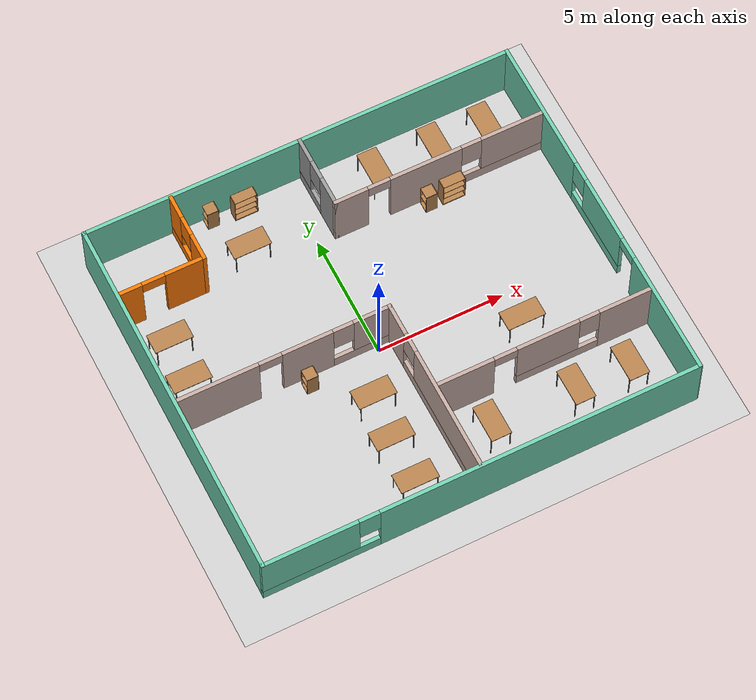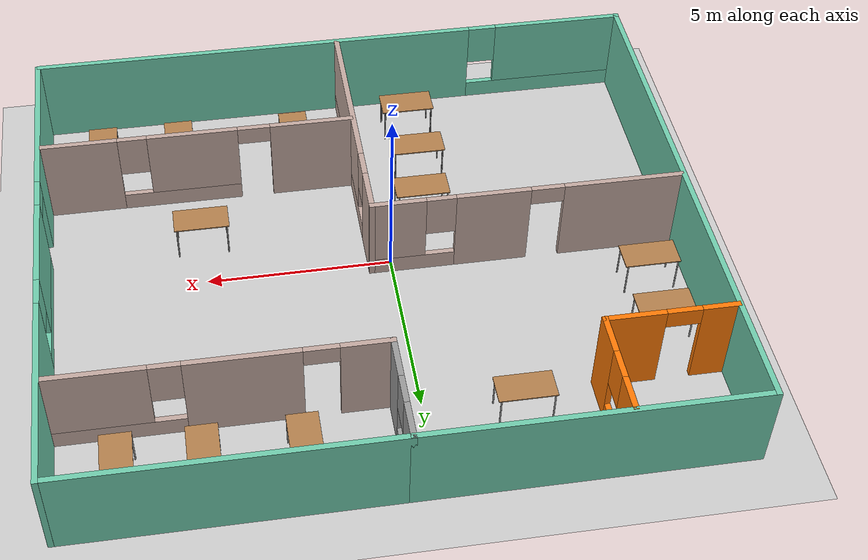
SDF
<sdf version="1.6">
 <world name="default">
  <model name="ground_plane">
   <static>1</static>
   <link name="link">
    <collision name="collision">
     <geometry><plane><normal>0 0 1</normal><size>100 100</size></plane></geometry>
     <surface>
      <contact><collide_bitmask>65535</collide_bitmask></contact>
      <friction><ode><mu>100</mu><mu2>50</mu2></ode></friction>
     </surface>
    </collision>
    <visual name="visual">
     <cast_shadows>0</cast_shadows>
     <geometry><plane><normal>0 0 1</normal><size>100 100</size></plane></geometry>
     <material>
      <script><uri>file://media/materials/scripts/gazebo.material</uri><name>Gazebo/Grey</name></script>
     </material>
    </visual>
   </link>
  </model>
  <light name="sun" type="directional">
   <pose>0 0 10 0 -0 0</pose>
   <diffuse>0.8 0.8 0.8 1</diffuse>
   <specular>0.2 0.2 0.2 1</specular>
   <attenuation>
    <range>1000</range>
    <constant>0.9</constant>
    <linear>0.01</linear>
    <quadratic>0.001</quadratic>
   </attenuation>
   <direction>-0.5 0.1 -0.9</direction>
  </light>
  <gravity>0 0 -9.8</gravity>
  <magnetic_field>6e-06 2.3e-05 -4.2e-05</magnetic_field>
  <atmosphere type="adiabatic"/>
  <physics name="default_physics" default="0" type="ode">
   <max_step_size>0.001</max_step_size>
   <real_time_factor>1</real_time_factor>
   <real_time_update_rate>1000</real_time_update_rate>
  </physics>
  <scene><ambient>0.4 0.4 0.4 1</ambient><background>0.7 0.7 0.7 1</background><shadows>1</shadows></scene>
  <spherical_coordinates>
   <surface_model>EARTH_WGS84</surface_model>
   <latitude_deg>0</latitude_deg>
   <longitude_deg>0</longitude_deg>
   <elevation>0</elevation>
   <heading_deg>0</heading_deg>
  </spherical_coordinates>
  <model name="building">
   <pose>0.669577 0.523003 0 0 -0 0</pose>
   <link name="Wall_0">
    <collision name="Wall_0_Collision">
     <geometry><box><size>14.75 0.15 2.5</size></box></geometry>
     <pose>0 0 1.25 0 -0 0</pose>
    </collision>
    <visual name="Wall_0_Visual">
     <pose>0 0 1.25 0 -0 0</pose>
     <geometry><box><size>14.75 0.15 2.5</size></box></geometry>
     <material>
      <script><uri>file://media/materials/scripts/gazebo.material</uri><name>Gazebo/Grey</name></script>
      <ambient>0.435294 0.796078 0.67451 1</ambient>
     </material>
     <meta><layer>0</layer></meta>
    </visual>
    <pose>-8.54234 0.004228 0 0 -0 1.5708</pose>
   </link>
   <link name="Wall_11">
    <pose>4.23266 4.39423 0 0 -0 0</pose>
    <visual name="Wall_11_Visual_0">
     <pose>-3.56356 0 1.25 0 -0 0</pose>
     <geometry><box><size>1.37289 0.15 2.5</size></box></geometry>
     <material>
      <script><uri>file://media/materials/scripts/gazebo.material</uri><name>Gazebo/Grey</name></script>
      <ambient>0.760784 0.662745 0.627451 1</ambient>
     </material>
     <meta><layer>0</layer></meta>
    </visual>
    <collision name="Wall_11_Collision_0">
     <geometry><box><size>1.37289 0.15 2.5</size></box></geometry>
     <pose>-3.56356 0 1.25 0 -0 0</pose>
    </collision>
    <visual name="Wall_11_Visual_1">
     <pose>-0.527181 0 1.25 0 -0 0</pose>
     <geometry><box><size>2.89987 0.15 2.5</size></box></geometry>
     <material>
      <script><uri>file://media/materials/scripts/gazebo.material</uri><name>Gazebo/Grey</name></script>
      <ambient>0.760784 0.662745 0.627451 1</ambient>
     </material>
     <meta><layer>0</layer></meta>
    </visual>
    <collision name="Wall_11_Collision_1">
     <geometry><box><size>2.89987 0.15 2.5</size></box></geometry>
     <pose>-0.527181 0 1.25 0 -0 0</pose>
    </collision>
    <visual name="Wall_11_Visual_2">
     <pose>2.58638 0 0.25 0 -0 0</pose>
     <geometry><box><size>3.32725 0.15 0.5</size></box></geometry>
     <material>
      <script><uri>file://media/materials/scripts/gazebo.material</uri><name>Gazebo/Grey</name></script>
      <ambient>0.760784 0.662745 0.627451 1</ambient>
     </material>
     <meta><layer>0</layer></meta>
    </visual>
    <collision name="Wall_11_Collision_2">
     <geometry><box><size>3.32725 0.15 0.5</size></box></geometry>
     <pose>2.58638 0 0.25 0 -0 0</pose>
    </collision>
    <visual name="Wall_11_Visual_3">
     <pose>2.98638 0 1.5 0 -0 0</pose>
     <geometry><box><size>2.52725 0.15 2</size></box></geometry>
     <material>
      <script><uri>file://media/materials/scripts/gazebo.material</uri><name>Gazebo/Grey</name></script>
      <ambient>0.760784 0.662745 0.627451 1</ambient>
     </material>
     <meta><layer>0</layer></meta>
    </visual>
    <collision name="Wall_11_Collision_3">
     <geometry><box><size>2.52725 0.15 2</size></box></geometry>
     <pose>2.98638 0 1.5 0 -0 0</pose>
    </collision>
    <visual name="Wall_11_Visual_4">
     <pose>1.32275 0 1.9 0 -0 0</pose>
     <geometry><box><size>0.8 0.15 1.2</size></box></geometry>
     <material>
      <script><uri>file://media/materials/scripts/gazebo.material</uri><name>Gazebo/Grey</name></script>
      <ambient>0.760784 0.662745 0.627451 1</ambient>
     </material>
     <meta><layer>0</layer></meta>
    </visual>
    <collision name="Wall_11_Collision_4">
     <geometry><box><size>0.8 0.15 1.2</size></box></geometry>
     <pose>1.32275 0 1.9 0 -0 0</pose>
    </collision>
    <visual name="Wall_11_Visual_5">
     <pose>-2.42711 0 2.25 0 -0 0</pose>
     <geometry><box><size>0.9 0.15 0.5</size></box></geometry>
     <material>
      <script><uri>file://media/materials/scripts/gazebo.material</uri><name>Gazebo/Grey</name></script>
      <ambient>0.760784 0.662745 0.627451 1</ambient>
     </material>
     <meta><layer>0</layer></meta>
    </visual>
    <collision name="Wall_11_Collision_5">
     <geometry><box><size>0.9 0.15 0.5</size></box></geometry>
     <pose>-2.42711 0 2.25 0 -0 0</pose>
    </collision>
   </link>
   <link name="Wall_13">
    <collision name="Wall_13_Collision">
     <geometry><box><size>8.5 0.15 2.5</size></box></geometry>
     <pose>0 0 1.25 0 -0 0</pose>
    </collision>
    <visual name="Wall_13_Visual">
     <pose>0 0 1.25 0 -0 0</pose>
     <geometry><box><size>8.5 0.15 2.5</size></box></geometry>
     <material>
      <script><uri>file://media/materials/scripts/gazebo.material</uri><name>Gazebo/Grey</name></script>
      <ambient>0.435294 0.796078 0.67451 1</ambient>
     </material>
     <meta><layer>0</layer></meta>
    </visual>
    <pose>4.23266 7.30423 0 0 -0 0</pose>
   </link>
   <link name="Wall_15">
    <pose>-4.28833 -0.269812 0 0 0 -4.6e-05</pose>
    <visual name="Wall_15_Visual_0">
     <pose>-2.61857 0 1.25 0 -0 0</pose>
     <geometry><box><size>3.26287 0.15 2.5</size></box></geometry>
     <material>
      <script><uri>file://media/materials/scripts/gazebo.material</uri><name>Gazebo/Grey</name></script>
      <ambient>0.760784 0.662745 0.627451 1</ambient>
     </material>
     <meta><layer>0</layer></meta>
    </visual>
    <collision name="Wall_15_Collision_0">
     <geometry><box><size>3.26287 0.15 2.5</size></box></geometry>
     <pose>-2.61857 0 1.25 0 -0 0</pose>
    </collision>
    <visual name="Wall_15_Visual_1">
     <pose>0.91749 0 1.25 0 -0 0</pose>
     <geometry><box><size>2.00924 0.15 2.5</size></box></geometry>
     <material>
      <script><uri>file://media/materials/scripts/gazebo.material</uri><name>Gazebo/Grey</name></script>
      <ambient>0.760784 0.662745 0.627451 1</ambient>
     </material>
     <meta><layer>0</layer></meta>
    </visual>
    <collision name="Wall_15_Collision_1">
     <geometry><box><size>2.00924 0.15 2.5</size></box></geometry>
     <pose>0.91749 0 1.25 0 -0 0</pose>
    </collision>
    <visual name="Wall_15_Visual_2">
     <pose>3.08605 0 0.25 0 -0 0</pose>
     <geometry><box><size>2.32789 0.15 0.5</size></box></geometry>
     <material>
      <script><uri>file://media/materials/scripts/gazebo.material</uri><name>Gazebo/Grey</name></script>
      <ambient>0.760784 0.662745 0.627451 1</ambient>
     </material>
     <meta><layer>0</layer></meta>
    </visual>
    <collision name="Wall_15_Collision_2">
     <geometry><box><size>2.32789 0.15 0.5</size></box></geometry>
     <pose>3.08605 0 0.25 0 -0 0</pose>
    </collision>
    <visual name="Wall_15_Visual_3">
     <pose>3.48605 0 1.5 0 -0 0</pose>
     <geometry><box><size>1.52789 0.15 2</size></box></geometry>
     <material>
      <script><uri>file://media/materials/scripts/gazebo.material</uri><name>Gazebo/Grey</name></script>
      <ambient>0.760784 0.662745 0.627451 1</ambient>
     </material>
     <meta><layer>0</layer></meta>
    </visual>
    <collision name="Wall_15_Collision_3">
     <geometry><box><size>1.52789 0.15 2</size></box></geometry>
     <pose>3.48605 0 1.5 0 -0 0</pose>
    </collision>
    <visual name="Wall_15_Visual_4">
     <pose>2.32211 0 1.9 0 -0 0</pose>
     <geometry><box><size>0.8 0.15 1.2</size></box></geometry>
     <material>
      <script><uri>file://media/materials/scripts/gazebo.material</uri><name>Gazebo/Grey</name></script>
      <ambient>0.760784 0.662745 0.627451 1</ambient>
     </material>
     <meta><layer>0</layer></meta>
    </visual>
    <collision name="Wall_15_Collision_4">
     <geometry><box><size>0.8 0.15 1.2</size></box></geometry>
     <pose>2.32211 0 1.9 0 -0 0</pose>
    </collision>
    <visual name="Wall_15_Visual_5">
     <pose>-0.537132 0 2.25 0 -0 0</pose>
     <geometry><box><size>0.9 0.15 0.5</size></box></geometry>
     <material>
      <script><uri>file://media/materials/scripts/gazebo.material</uri><name>Gazebo/Grey</name></script>
      <ambient>0.760784 0.662745 0.627451 1</ambient>
     </material>
     <meta><layer>0</layer></meta>
    </visual>
    <collision name="Wall_15_Collision_5">
     <geometry><box><size>0.9 0.15 0.5</size></box></geometry>
     <pose>-0.537132 0 2.25 0 -0 0</pose>
    </collision>
   </link>
   <link name="Wall_16">
    <pose>-0.113577 -3.745 0 0 0 -1.5708</pose>
    <visual name="Wall_16_Visual_0">
     <pose>-2.88983 0 1.25 0 -0 0</pose>
     <geometry><box><size>1.32035 0.15 2.5</size></box></geometry>
     <material>
      <script><uri>file://media/materials/scripts/gazebo.material</uri><name>Gazebo/Grey</name></script>
      <ambient>0.760784 0.662745 0.627451 1</ambient>
     </material>
     <meta><layer>0</layer></meta>
    </visual>
    <collision name="Wall_16_Collision_0">
     <geometry><box><size>1.32035 0.15 2.5</size></box></geometry>
     <pose>-2.88983 0 1.25 0 -0 0</pose>
    </collision>
    <visual name="Wall_16_Visual_1">
     <pose>0.660174 0 0.25 0 -0 0</pose>
     <geometry><box><size>5.77965 0.15 0.5</size></box></geometry>
     <material>
      <script><uri>file://media/materials/scripts/gazebo.material</uri><name>Gazebo/Grey</name></script>
      <ambient>0.760784 0.662745 0.627451 1</ambient>
     </material>
     <meta><layer>0</layer></meta>
    </visual>
    <collision name="Wall_16_Collision_1">
     <geometry><box><size>5.77965 0.15 0.5</size></box></geometry>
     <pose>0.660174 0 0.25 0 -0 0</pose>
    </collision>
    <visual name="Wall_16_Visual_2">
     <pose>1.06017 0 1.5 0 -0 0</pose>
     <geometry><box><size>4.97965 0.15 2</size></box></geometry>
     <material>
      <script><uri>file://media/materials/scripts/gazebo.material</uri><name>Gazebo/Grey</name></script>
      <ambient>0.760784 0.662745 0.627451 1</ambient>
     </material>
     <meta><layer>0</layer></meta>
    </visual>
    <collision name="Wall_16_Collision_2">
     <geometry><box><size>4.97965 0.15 2</size></box></geometry>
     <pose>1.06017 0 1.5 0 -0 0</pose>
    </collision>
    <visual name="Wall_16_Visual_3">
     <pose>-1.82965 0 1.9 0 -0 0</pose>
     <geometry><box><size>0.8 0.15 1.2</size></box></geometry>
     <material>
      <script><uri>file://media/materials/scripts/gazebo.material</uri><name>Gazebo/Grey</name></script>
      <ambient>0.760784 0.662745 0.627451 1</ambient>
     </material>
     <meta><layer>0</layer></meta>
    </visual>
    <collision name="Wall_16_Collision_3">
     <geometry><box><size>0.8 0.15 1.2</size></box></geometry>
     <pose>-1.82965 0 1.9 0 -0 0</pose>
    </collision>
   </link>
   <link name="Wall_18">
    <pose>4.19252 -3.81906 0 0 -0 3.14159</pose>
    <visual name="Wall_18_Visual_0">
     <pose>-3.25532 0 1.25 0 -0 0</pose>
     <geometry><box><size>2.08936 0.15 2.5</size></box></geometry>
     <material>
      <script><uri>file://media/materials/scripts/gazebo.material</uri><name>Gazebo/Grey</name></script>
      <ambient>0.760784 0.662745 0.627451 1</ambient>
     </material>
     <meta><layer>0</layer></meta>
    </visual>
    <collision name="Wall_18_Collision_0">
     <geometry><box><size>2.08936 0.15 2.5</size></box></geometry>
     <pose>-3.25532 0 1.25 0 -0 0</pose>
    </collision>
    <visual name="Wall_18_Visual_1">
     <pose>3.14264 0 1.25 0 -0 0</pose>
     <geometry><box><size>2.31472 0.15 2.5</size></box></geometry>
     <material>
      <script><uri>file://media/materials/scripts/gazebo.material</uri><name>Gazebo/Grey</name></script>
      <ambient>0.760784 0.662745 0.627451 1</ambient>
     </material>
     <meta><layer>0</layer></meta>
    </visual>
    <collision name="Wall_18_Collision_1">
     <geometry><box><size>2.31472 0.15 2.5</size></box></geometry>
     <pose>3.14264 0 1.25 0 -0 0</pose>
    </collision>
    <visual name="Wall_18_Visual_2">
     <pose>-0.562678 0 0.25 0 -0 0</pose>
     <geometry><box><size>3.29592 0.15 0.5</size></box></geometry>
     <material>
      <script><uri>file://media/materials/scripts/gazebo.material</uri><name>Gazebo/Grey</name></script>
      <ambient>0.760784 0.662745 0.627451 1</ambient>
     </material>
     <meta><layer>0</layer></meta>
    </visual>
    <collision name="Wall_18_Collision_2">
     <geometry><box><size>3.29592 0.15 0.5</size></box></geometry>
     <pose>-0.562678 0 0.25 0 -0 0</pose>
    </collision>
    <visual name="Wall_18_Visual_3">
     <pose>-0.162678 0 1.5 0 -0 0</pose>
     <geometry><box><size>2.49593 0.15 2</size></box></geometry>
     <material>
      <script><uri>file://media/materials/scripts/gazebo.material</uri><name>Gazebo/Grey</name></script>
      <ambient>0.760784 0.662745 0.627451 1</ambient>
     </material>
     <meta><layer>0</layer></meta>
    </visual>
    <collision name="Wall_18_Collision_3">
     <geometry><box><size>2.49593 0.15 2</size></box></geometry>
     <pose>-0.162678 0 1.5 0 -0 0</pose>
    </collision>
    <visual name="Wall_18_Visual_4">
     <pose>-1.81064 0 1.9 0 -0 0</pose>
     <geometry><box><size>0.8 0.15 1.2</size></box></geometry>
     <material>
      <script><uri>file://media/materials/scripts/gazebo.material</uri><name>Gazebo/Grey</name></script>
      <ambient>0.760784 0.662745 0.627451 1</ambient>
     </material>
     <meta><layer>0</layer></meta>
    </visual>
    <collision name="Wall_18_Collision_4">
     <geometry><box><size>0.8 0.15 1.2</size></box></geometry>
     <pose>-1.81064 0 1.9 0 -0 0</pose>
    </collision>
    <visual name="Wall_18_Visual_5">
     <pose>1.53528 0 2.25 0 -0 0</pose>
     <geometry><box><size>0.9 0.15 0.5</size></box></geometry>
     <material>
      <script><uri>file://media/materials/scripts/gazebo.material</uri><name>Gazebo/Grey</name></script>
      <ambient>0.760784 0.662745 0.627451 1</ambient>
     </material>
     <meta><layer>0</layer></meta>
    </visual>
    <collision name="Wall_18_Collision_5">
     <geometry><box><size>0.9 0.15 0.5</size></box></geometry>
     <pose>1.53528 0 2.25 0 -0 0</pose>
    </collision>
   </link>
   <link name="Wall_2">
    <pose>8.54758 0.007002 0 0 0 -1.5708</pose>
    <visual name="Wall_2_Visual_0">
     <pose>-4.65754 0 1.25 0 -0 0</pose>
     <geometry><box><size>5.43493 0.15 2.5</size></box></geometry>
     <material>
      <script><uri>file://media/materials/scripts/gazebo.material</uri><name>Gazebo/Grey</name></script>
      <ambient>0.435294 0.796078 0.67451 1</ambient>
     </material>
     <meta><layer>0</layer></meta>
    </visual>
    <collision name="Wall_2_Collision_0">
     <geometry><box><size>5.43493 0.15 2.5</size></box></geometry>
     <pose>-4.65754 0 1.25 0 -0 0</pose>
    </collision>
    <visual name="Wall_2_Visual_1">
     <pose>4.92366 0 1.25 0 -0 0</pose>
     <geometry><box><size>4.90268 0.15 2.5</size></box></geometry>
     <material>
      <script><uri>file://media/materials/scripts/gazebo.material</uri><name>Gazebo/Grey</name></script>
      <ambient>0.435294 0.796078 0.67451 1</ambient>
     </material>
     <meta><layer>0</layer></meta>
    </visual>
    <collision name="Wall_2_Collision_1">
     <geometry><box><size>4.90268 0.15 2.5</size></box></geometry>
     <pose>4.92366 0 1.25 0 -0 0</pose>
    </collision>
    <visual name="Wall_2_Visual_2">
     <pose>-0.183873 0 0.25 0 -0 0</pose>
     <geometry><box><size>3.51239 0.15 0.5</size></box></geometry>
     <material>
      <script><uri>file://media/materials/scripts/gazebo.material</uri><name>Gazebo/Grey</name></script>
      <ambient>0.435294 0.796078 0.67451 1</ambient>
     </material>
     <meta><layer>0</layer></meta>
    </visual>
    <collision name="Wall_2_Collision_2">
     <geometry><box><size>3.51239 0.15 0.5</size></box></geometry>
     <pose>-0.183873 0 0.25 0 -0 0</pose>
    </collision>
    <visual name="Wall_2_Visual_3">
     <pose>0.216127 0 1.5 0 -0 0</pose>
     <geometry><box><size>2.71239 0.15 2</size></box></geometry>
     <material>
      <script><uri>file://media/materials/scripts/gazebo.material</uri><name>Gazebo/Grey</name></script>
      <ambient>0.435294 0.796078 0.67451 1</ambient>
     </material>
     <meta><layer>0</layer></meta>
    </visual>
    <collision name="Wall_2_Collision_3">
     <geometry><box><size>2.71239 0.15 2</size></box></geometry>
     <pose>0.216127 0 1.5 0 -0 0</pose>
    </collision>
    <visual name="Wall_2_Visual_4">
     <pose>-1.54007 0 1.9 0 -0 0</pose>
     <geometry><box><size>0.8 0.15 1.2</size></box></geometry>
     <material>
      <script><uri>file://media/materials/scripts/gazebo.material</uri><name>Gazebo/Grey</name></script>
      <ambient>0.435294 0.796078 0.67451 1</ambient>
     </material>
     <meta><layer>0</layer></meta>
    </visual>
    <collision name="Wall_2_Collision_4">
     <geometry><box><size>0.8 0.15 1.2</size></box></geometry>
     <pose>-1.54007 0 1.9 0 -0 0</pose>
    </collision>
    <visual name="Wall_2_Visual_5">
     <pose>2.02232 0 2.25 0 -0 0</pose>
     <geometry><box><size>0.9 0.15 0.5</size></box></geometry>
     <material>
      <script><uri>file://media/materials/scripts/gazebo.material</uri><name>Gazebo/Grey</name></script>
      <ambient>0.435294 0.796078 0.67451 1</ambient>
     </material>
     <meta><layer>0</layer></meta>
    </visual>
    <collision name="Wall_2_Collision_5">
     <geometry><box><size>0.9 0.15 0.5</size></box></geometry>
     <pose>2.02232 0 2.25 0 -0 0</pose>
    </collision>
   </link>
   <link name="Wall_20">
    <pose>-6.81011 4.48629 0 0 -0 0</pose>
    <visual name="Wall_20_Visual_0">
     <pose>-1.26355 0 1.25 0 -0 0</pose>
     <geometry><box><size>0.972906 0.15 2.5</size></box></geometry>
     <material>
      <script><uri>file://media/materials/scripts/gazebo.material</uri><name>Gazebo/Grey</name></script>
      <ambient>0.996078 0.47451 0.0196078 1</ambient>
     </material>
     <meta><layer>0</layer></meta>
    </visual>
    <collision name="Wall_20_Collision_0">
     <geometry><box><size>0.972906 0.15 2.5</size></box></geometry>
     <pose>-1.26355 0 1.25 0 -0 0</pose>
    </collision>
    <visual name="Wall_20_Visual_1">
     <pose>0.936453 0 1.25 0 -0 0</pose>
     <geometry><box><size>1.62709 0.15 2.5</size></box></geometry>
     <material>
      <script><uri>file://media/materials/scripts/gazebo.material</uri><name>Gazebo/Grey</name></script>
      <ambient>0.996078 0.47451 0.0196078 1</ambient>
     </material>
     <meta><layer>0</layer></meta>
    </visual>
    <collision name="Wall_20_Collision_1">
     <geometry><box><size>1.62709 0.15 2.5</size></box></geometry>
     <pose>0.936453 0 1.25 0 -0 0</pose>
    </collision>
    <visual name="Wall_20_Visual_2">
     <pose>-0.327094 0 2.25 0 -0 0</pose>
     <geometry><box><size>0.9 0.15 0.5</size></box></geometry>
     <material>
      <script><uri>file://media/materials/scripts/gazebo.material</uri><name>Gazebo/Grey</name></script>
      <ambient>0.996078 0.47451 0.0196078 1</ambient>
     </material>
     <meta><layer>0</layer></meta>
    </visual>
    <collision name="Wall_20_Collision_2">
     <geometry><box><size>0.9 0.15 0.5</size></box></geometry>
     <pose>-0.327094 0 2.25 0 -0 0</pose>
    </collision>
   </link>
   <link name="Wall_21">
    <pose>-5.13511 5.86129 0 0 -0 1.5708</pose>
    <visual name="Wall_21_Visual_0">
     <pose>-0.89205 0 1.25 0 -0 0</pose>
     <geometry><box><size>1.1159 0.15 2.5</size></box></geometry>
     <material>
      <script><uri>file://media/materials/scripts/gazebo.material</uri><name>Gazebo/Grey</name></script>
      <ambient>0.996078 0.47451 0.0196078 1</ambient>
     </material>
     <meta><layer>0</layer></meta>
    </visual>
    <collision name="Wall_21_Collision_0">
     <geometry><box><size>1.1159 0.15 2.5</size></box></geometry>
     <pose>-0.89205 0 1.25 0 -0 0</pose>
    </collision>
    <visual name="Wall_21_Visual_1">
     <pose>0.55795 0 0.25 0 -0 0</pose>
     <geometry><box><size>1.7841 0.15 0.5</size></box></geometry>
     <material>
      <script><uri>file://media/materials/scripts/gazebo.material</uri><name>Gazebo/Grey</name></script>
      <ambient>0.996078 0.47451 0.0196078 1</ambient>
     </material>
     <meta><layer>0</layer></meta>
    </visual>
    <collision name="Wall_21_Collision_1">
     <geometry><box><size>1.7841 0.15 0.5</size></box></geometry>
     <pose>0.55795 0 0.25 0 -0 0</pose>
    </collision>
    <visual name="Wall_21_Visual_2">
     <pose>0.95795 0 1.5 0 -0 0</pose>
     <geometry><box><size>0.9841 0.15 2</size></box></geometry>
     <material>
      <script><uri>file://media/materials/scripts/gazebo.material</uri><name>Gazebo/Grey</name></script>
      <ambient>0.996078 0.47451 0.0196078 1</ambient>
     </material>
     <meta><layer>0</layer></meta>
    </visual>
    <collision name="Wall_21_Collision_2">
     <geometry><box><size>0.9841 0.15 2</size></box></geometry>
     <pose>0.95795 0 1.5 0 -0 0</pose>
    </collision>
    <visual name="Wall_21_Visual_3">
     <pose>0.0659 0 1.9 0 -0 0</pose>
     <geometry><box><size>0.8 0.15 1.2</size></box></geometry>
     <material>
      <script><uri>file://media/materials/scripts/gazebo.material</uri><name>Gazebo/Grey</name></script>
      <ambient>0.996078 0.47451 0.0196078 1</ambient>
     </material>
     <meta><layer>0</layer></meta>
    </visual>
    <collision name="Wall_21_Collision_3">
     <geometry><box><size>0.8 0.15 1.2</size></box></geometry>
     <pose>0.0659 0 1.9 0 -0 0</pose>
    </collision>
   </link>
   <link name="Wall_24">
    <pose>0.057659 5.84923 0 0 -0 1.5708</pose>
    <visual name="Wall_24_Visual_0">
     <pose>-0.929516 0 1.25 0 -0 0</pose>
     <geometry><box><size>1.20097 0.15 2.5</size></box></geometry>
     <material>
      <script><uri>file://media/materials/scripts/gazebo.material</uri><name>Gazebo/Grey</name></script>
      <ambient>1 1 1 1</ambient>
     </material>
     <meta><layer>0</layer></meta>
    </visual>
    <collision name="Wall_24_Collision_0">
     <geometry><box><size>1.20097 0.15 2.5</size></box></geometry>
     <pose>-0.929516 0 1.25 0 -0 0</pose>
    </collision>
    <visual name="Wall_24_Visual_1">
     <pose>0.600484 0 0.25 0 -0 0</pose>
     <geometry><box><size>1.85903 0.15 0.5</size></box></geometry>
     <material>
      <script><uri>file://media/materials/scripts/gazebo.material</uri><name>Gazebo/Grey</name></script>
      <ambient>1 1 1 1</ambient>
     </material>
     <meta><layer>0</layer></meta>
    </visual>
    <collision name="Wall_24_Collision_1">
     <geometry><box><size>1.85903 0.15 0.5</size></box></geometry>
     <pose>0.600484 0 0.25 0 -0 0</pose>
    </collision>
    <visual name="Wall_24_Visual_2">
     <pose>1.00048 0 1.5 0 -0 0</pose>
     <geometry><box><size>1.05903 0.15 2</size></box></geometry>
     <material>
      <script><uri>file://media/materials/scripts/gazebo.material</uri><name>Gazebo/Grey</name></script>
      <ambient>1 1 1 1</ambient>
     </material>
     <meta><layer>0</layer></meta>
    </visual>
    <collision name="Wall_24_Collision_2">
     <geometry><box><size>1.05903 0.15 2</size></box></geometry>
     <pose>1.00048 0 1.5 0 -0 0</pose>
    </collision>
    <visual name="Wall_24_Visual_3">
     <pose>0.070969 0 1.9 0 -0 0</pose>
     <geometry><box><size>0.8 0.15 1.2</size></box></geometry>
     <material>
      <script><uri>file://media/materials/scripts/gazebo.material</uri><name>Gazebo/Grey</name></script>
      <ambient>1 1 1 1</ambient>
     </material>
     <meta><layer>0</layer></meta>
    </visual>
    <collision name="Wall_24_Collision_3">
     <geometry><box><size>0.8 0.15 1.2</size></box></geometry>
     <pose>0.070969 0 1.9 0 -0 0</pose>
    </collision>
   </link>
   <link name="Wall_7">
    <pose>-0.022577 -7.307 0 0 -0 3.14159</pose>
    <visual name="Wall_7_Visual_0">
     <pose>-2.28106 0 1.25 0 -0 0</pose>
     <geometry><box><size>12.6379 0.15 2.5</size></box></geometry>
     <material>
      <script><uri>file://media/materials/scripts/gazebo.material</uri><name>Gazebo/Grey</name></script>
      <ambient>0.435294 0.796078 0.67451 1</ambient>
     </material>
     <meta><layer>0</layer></meta>
    </visual>
    <collision name="Wall_7_Collision_0">
     <geometry><box><size>12.6379 0.15 2.5</size></box></geometry>
     <pose>-2.28106 0 1.25 0 -0 0</pose>
    </collision>
    <visual name="Wall_7_Visual_1">
     <pose>6.31894 0 0.25 0 -0 0</pose>
     <geometry><box><size>4.56212 0.15 0.5</size></box></geometry>
     <material>
      <script><uri>file://media/materials/scripts/gazebo.material</uri><name>Gazebo/Grey</name></script>
      <ambient>0.435294 0.796078 0.67451 1</ambient>
     </material>
     <meta><layer>0</layer></meta>
    </visual>
    <collision name="Wall_7_Collision_1">
     <geometry><box><size>4.56212 0.15 0.5</size></box></geometry>
     <pose>6.31894 0 0.25 0 -0 0</pose>
    </collision>
    <visual name="Wall_7_Visual_2">
     <pose>6.71894 0 1.5 0 -0 0</pose>
     <geometry><box><size>3.76212 0.15 2</size></box></geometry>
     <material>
      <script><uri>file://media/materials/scripts/gazebo.material</uri><name>Gazebo/Grey</name></script>
      <ambient>0.435294 0.796078 0.67451 1</ambient>
     </material>
     <meta><layer>0</layer></meta>
    </visual>
    <collision name="Wall_7_Collision_2">
     <geometry><box><size>3.76212 0.15 2</size></box></geometry>
     <pose>6.71894 0 1.5 0 -0 0</pose>
    </collision>
    <visual name="Wall_7_Visual_3">
     <pose>4.43788 0 1.9 0 -0 0</pose>
     <geometry><box><size>0.8 0.15 1.2</size></box></geometry>
     <material>
      <script><uri>file://media/materials/scripts/gazebo.material</uri><name>Gazebo/Grey</name></script>
      <ambient>0.435294 0.796078 0.67451 1</ambient>
     </material>
     <meta><layer>0</layer></meta>
    </visual>
    <collision name="Wall_7_Collision_3">
     <geometry><box><size>0.8 0.15 1.2</size></box></geometry>
     <pose>4.43788 0 1.9 0 -0 0</pose>
    </collision>
   </link>
   <link name="Wall_9">
    <collision name="Wall_9_Collision">
     <geometry><box><size>8.75 0.15 2.5</size></box></geometry>
     <pose>0 0 1.25 0 -0 0</pose>
    </collision>
    <visual name="Wall_9_Visual">
     <pose>0 0 1.25 0 -0 0</pose>
     <geometry><box><size>8.75 0.15 2.5</size></box></geometry>
     <material>
      <script><uri>file://media/materials/scripts/gazebo.material</uri><name>Gazebo/Grey</name></script>
      <ambient>0.435294 0.796078 0.67451 1</ambient>
     </material>
     <meta><layer>0</layer></meta>
    </visual>
    <pose>-4.24234 7.30423 0 0 -0 0</pose>
   </link>
   <static>1</static>
  </model>
  <model name="bookshelf">
   <static>1</static>
   <link name="link">
    <inertial><mass>1</mass></inertial>
    <collision name="back">
     <pose>0 0.005 0.6 0 -0 0</pose>
     <geometry><box><size>0.9 0.01 1.2</size></box></geometry>
    </collision>
    <visual name="visual1">
     <pose>0 0.005 0.6 0 -0 0</pose>
     <geometry><box><size>0.9 0.01 1.2</size></box></geometry>
     <material>
      <script><uri>file://media/materials/scripts/gazebo.material</uri><name>Gazebo/Wood</name></script>
     </material>
    </visual>
    <collision name="left_side">
     <pose>0.45 -0.195 0.6 0 -0 0</pose>
     <geometry><box><size>0.02 0.4 1.2</size></box></geometry>
    </collision>
    <visual name="visual2">
     <pose>0.45 -0.195 0.6 0 -0 0</pose>
     <geometry><box><size>0.02 0.4 1.2</size></box></geometry>
     <material>
      <script><uri>file://media/materials/scripts/gazebo.material</uri><name>Gazebo/Wood</name></script>
     </material>
    </visual>
    <collision name="right_side">
     <pose>-0.45 -0.195 0.6 0 -0 0</pose>
     <geometry><box><size>0.02 0.4 1.2</size></box></geometry>
    </collision>
    <visual name="visual3">
     <pose>-0.45 -0.195 0.6 0 -0 0</pose>
     <geometry><box><size>0.02 0.4 1.2</size></box></geometry>
     <material>
      <script><uri>file://media/materials/scripts/gazebo.material</uri><name>Gazebo/Wood</name></script>
     </material>
    </visual>
    <collision name="bottom">
     <pose>0 -0.195 0.03 0 -0 0</pose>
     <geometry><box><size>0.88 0.4 0.06</size></box></geometry>
    </collision>
    <visual name="visual4">
     <pose>0 -0.195 0.03 0 -0 0</pose>
     <geometry><box><size>0.88 0.4 0.06</size></box></geometry>
     <material>
      <script><uri>file://media/materials/scripts/gazebo.material</uri><name>Gazebo/Wood</name></script>
     </material>
    </visual>
    <collision name="top">
     <pose>0 -0.195 1.19 0 -0 0</pose>
     <geometry><box><size>0.88 0.4 0.02</size></box></geometry>
    </collision>
    <visual name="visual5">
     <pose>0 -0.195 1.19 0 -0 0</pose>
     <geometry><box><size>0.88 0.4 0.02</size></box></geometry>
     <material>
      <script><uri>file://media/materials/scripts/gazebo.material</uri><name>Gazebo/Wood</name></script>
     </material>
    </visual>
    <collision name="low_shelf">
     <pose>0 -0.195 0.43 0 -0 0</pose>
     <geometry><box><size>0.88 0.4 0.02</size></box></geometry>
    </collision>
    <visual name="visual6">
     <pose>0 -0.195 0.43 0 -0 0</pose>
     <geometry><box><size>0.88 0.4 0.02</size></box></geometry>
     <material>
      <script><uri>file://media/materials/scripts/gazebo.material</uri><name>Gazebo/Wood</name></script>
     </material>
    </visual>
    <collision name="high_shelf">
     <pose>0 -0.195 0.8 0 -0 0</pose>
     <geometry><box><size>0.88 0.4 0.02</size></box></geometry>
    </collision>
    <visual name="visual7">
     <pose>0 -0.195 0.8 0 -0 0</pose>
     <geometry><box><size>0.88 0.4 0.02</size></box></geometry>
     <material>
      <script><uri>file://media/materials/scripts/gazebo.material</uri><name>Gazebo/Wood</name></script>
     </material>
    </visual>
   </link>
   <pose>-1.80246 7.56703 0 0 -0 0</pose>
  </model>
  <model name="cabinet">
   <static>1</static>
   <link name="cabinet_bottom_plate">
    <inertial>
     <pose>0 0 -1 0 -0 0</pose>
     <inertia><ixx>2.05</ixx><ixy>0</ixy><ixz>0</ixz><iyy>2.05</iyy><iyz>0</iyz><izz>2.05</izz></inertia>
     <mass>25</mass>
    </inertial>
    <collision name="cabinet_bottom_plate_geom">
     <pose>0 0 0.01 0 -0 0</pose>
     <geometry><box><size>0.45 0.45 0.02</size></box></geometry>
    </collision>
    <visual name="cabinet_bottom_plate_geom_visual">
     <pose>0 0 0.01 0 -0 0</pose>
     <geometry><box><size>0.45 0.45 0.02</size></box></geometry>
     <material>
      <script><uri>file://media/materials/scripts/gazebo.material</uri><name>Gazebo/Wood</name></script>
     </material>
    </visual>
    <collision name="cabinet_bottom_plate_geom_cabinet_back_plate">
     <pose>0.235 0 0.51 0 -0 0</pose>
     <geometry><box><size>0.02 0.45 1.02</size></box></geometry>
    </collision>
    <visual name="cabinet_bottom_plate_geom_cabinet_back_plate_visual">
     <pose>0.235 0 0.51 0 -0 0</pose>
     <geometry><box><size>0.02 0.45 1.02</size></box></geometry>
     <material>
      <script><uri>file://media/materials/scripts/gazebo.material</uri><name>Gazebo/Wood</name></script>
     </material>
    </visual>
    <collision name="cabinet_bottom_plate_geom_cabinet_left_plate">
     <pose>0 0.235 0.51 0 -0 0</pose>
     <geometry><box><size>0.45 0.02 1.02</size></box></geometry>
    </collision>
    <visual name="cabinet_bottom_plate_geom_cabinet_left_plate_visual">
     <pose>0 0.235 0.51 0 -0 0</pose>
     <geometry><box><size>0.45 0.02 1.02</size></box></geometry>
     <material>
      <script><uri>file://media/materials/scripts/gazebo.material</uri><name>Gazebo/Wood</name></script>
     </material>
    </visual>
    <collision name="cabinet_bottom_plate_geom_cabinet_middle_plate">
     <pose>0 0 0.51 0 -0 0</pose>
     <geometry><box><size>0.45 0.45 0.02</size></box></geometry>
    </collision>
    <visual name="cabinet_bottom_plate_geom_cabinet_middle_plate_visual">
     <pose>0 0 0.51 0 -0 0</pose>
     <geometry><box><size>0.45 0.45 0.02</size></box></geometry>
     <material>
      <script><uri>file://media/materials/scripts/gazebo.material</uri><name>Gazebo/Wood</name></script>
     </material>
    </visual>
    <collision name="cabinet_bottom_plate_geom_cabinet_right_plate">
     <pose>0 -0.235 0.51 0 -0 0</pose>
     <geometry><box><size>0.45 0.02 1.02</size></box></geometry>
    </collision>
    <visual name="cabinet_bottom_plate_geom_cabinet_right_plate_visual">
     <pose>0 -0.235 0.51 0 -0 0</pose>
     <geometry><box><size>0.45 0.02 1.02</size></box></geometry>
     <material>
      <script><uri>file://media/materials/scripts/gazebo.material</uri><name>Gazebo/Wood</name></script>
     </material>
    </visual>
    <collision name="cabinet_bottom_plate_geom_cabinet_top_plate">
     <pose>0 0 1.01 0 -0 0</pose>
     <geometry><box><size>0.45 0.45 0.02</size></box></geometry>
    </collision>
    <visual name="cabinet_bottom_plate_geom_cabinet_top_plate_visual">
     <pose>0 0 1.01 0 -0 0</pose>
     <geometry><box><size>0.45 0.45 0.02</size></box></geometry>
     <material>
      <script><uri>file://media/materials/scripts/gazebo.material</uri><name>Gazebo/Wood</name></script>
     </material>
    </visual>
   </link>
   <pose>-3.08621 7.53379 0 0 -0 0</pose>
  </model>
  <model name="table">
   <static>1</static>
   <link name="link">
    <collision name="surface">
     <pose>0 0 1 0 -0 0</pose>
     <geometry><box><size>1.5 0.8 0.03</size></box></geometry>
     <surface><friction><ode><mu>0.6</mu><mu2>0.6</mu2></ode></friction></surface>
    </collision>
    <visual name="visual1">
     <pose>0 0 1 0 -0 0</pose>
     <geometry><box><size>1.5 0.8 0.03</size></box></geometry>
     <material>
      <script><uri>file://media/materials/scripts/gazebo.material</uri><name>Gazebo/Wood</name></script>
     </material>
    </visual>
    <collision name="front_left_leg">
     <pose>0.68 0.38 0.5 0 -0 0</pose>
     <geometry><cylinder><radius>0.02</radius><length>1</length></cylinder></geometry>
    </collision>
    <visual name="front_left_leg">
     <pose>0.68 0.38 0.5 0 -0 0</pose>
     <geometry><cylinder><radius>0.02</radius><length>1</length></cylinder></geometry>
     <material>
      <script><uri>file://media/materials/scripts/gazebo.material</uri><name>Gazebo/Grey</name></script>
     </material>
    </visual>
    <collision name="front_right_leg">
     <pose>0.68 -0.38 0.5 0 -0 0</pose>
     <geometry><cylinder><radius>0.02</radius><length>1</length></cylinder></geometry>
    </collision>
    <visual name="front_right_leg">
     <pose>0.68 -0.38 0.5 0 -0 0</pose>
     <geometry><cylinder><radius>0.02</radius><length>1</length></cylinder></geometry>
     <material>
      <script><uri>file://media/materials/scripts/gazebo.material</uri><name>Gazebo/Grey</name></script>
     </material>
    </visual>
    <collision name="back_right_leg">
     <pose>-0.68 -0.38 0.5 0 -0 0</pose>
     <geometry><cylinder><radius>0.02</radius><length>1</length></cylinder></geometry>
    </collision>
    <visual name="back_right_leg">
     <pose>-0.68 -0.38 0.5 0 -0 0</pose>
     <geometry><cylinder><radius>0.02</radius><length>1</length></cylinder></geometry>
     <material>
      <script><uri>file://media/materials/scripts/gazebo.material</uri><name>Gazebo/Grey</name></script>
     </material>
    </visual>
    <collision name="back_left_leg">
     <pose>-0.68 0.38 0.5 0 -0 0</pose>
     <geometry><cylinder><radius>0.02</radius><length>1</length></cylinder></geometry>
    </collision>
    <visual name="back_left_leg">
     <pose>-0.68 0.38 0.5 0 -0 0</pose>
     <geometry><cylinder><radius>0.02</radius><length>1</length></cylinder></geometry>
     <material>
      <script><uri>file://media/materials/scripts/gazebo.material</uri><name>Gazebo/Grey</name></script>
     </material>
    </visual>
   </link>
   <pose>-2.46357 5.61264 0 0 -0 0</pose>
  </model>
  <model name="table_clone">
   <static>1</static>
   <link name="link">
    <collision name="surface">
     <pose>0 0 1 0 -0 0</pose>
     <geometry><box><size>1.5 0.8 0.03</size></box></geometry>
     <surface><friction><ode><mu>0.6</mu><mu2>0.6</mu2></ode></friction></surface>
    </collision>
    <visual name="visual1">
     <pose>0 0 1 0 -0 0</pose>
     <geometry><box><size>1.5 0.8 0.03</size></box></geometry>
     <material>
      <script><uri>file://media/materials/scripts/gazebo.material</uri><name>Gazebo/Wood</name></script>
     </material>
    </visual>
    <collision name="front_left_leg">
     <pose>0.68 0.38 0.5 0 -0 0</pose>
     <geometry><cylinder><radius>0.02</radius><length>1</length></cylinder></geometry>
    </collision>
    <visual name="front_left_leg">
     <pose>0.68 0.38 0.5 0 -0 0</pose>
     <geometry><cylinder><radius>0.02</radius><length>1</length></cylinder></geometry>
     <material>
      <script><uri>file://media/materials/scripts/gazebo.material</uri><name>Gazebo/Grey</name></script>
     </material>
    </visual>
    <collision name="front_right_leg">
     <pose>0.68 -0.38 0.5 0 -0 0</pose>
     <geometry><cylinder><radius>0.02</radius><length>1</length></cylinder></geometry>
    </collision>
    <visual name="front_right_leg">
     <pose>0.68 -0.38 0.5 0 -0 0</pose>
     <geometry><cylinder><radius>0.02</radius><length>1</length></cylinder></geometry>
     <material>
      <script><uri>file://media/materials/scripts/gazebo.material</uri><name>Gazebo/Grey</name></script>
     </material>
    </visual>
    <collision name="back_right_leg">
     <pose>-0.68 -0.38 0.5 0 -0 0</pose>
     <geometry><cylinder><radius>0.02</radius><length>1</length></cylinder></geometry>
    </collision>
    <visual name="back_right_leg">
     <pose>-0.68 -0.38 0.5 0 -0 0</pose>
     <geometry><cylinder><radius>0.02</radius><length>1</length></cylinder></geometry>
     <material>
      <script><uri>file://media/materials/scripts/gazebo.material</uri><name>Gazebo/Grey</name></script>
     </material>
    </visual>
    <collision name="back_left_leg">
     <pose>-0.68 0.38 0.5 0 -0 0</pose>
     <geometry><cylinder><radius>0.02</radius><length>1</length></cylinder></geometry>
    </collision>
    <visual name="back_left_leg">
     <pose>-0.68 0.38 0.5 0 -0 0</pose>
     <geometry><cylinder><radius>0.02</radius><length>1</length></cylinder></geometry>
     <material>
      <script><uri>file://media/materials/scripts/gazebo.material</uri><name>Gazebo/Grey</name></script>
     </material>
    </visual>
   </link>
   <pose>-6.73253 1.64602 0 0 -0 0</pose>
  </model>
  <model name="table_clone_0">
   <static>1</static>
   <link name="link">
    <collision name="surface">
     <pose>0 0 1 0 -0 0</pose>
     <geometry><box><size>1.5 0.8 0.03</size></box></geometry>
     <surface><friction><ode><mu>0.6</mu><mu2>0.6</mu2></ode></friction></surface>
    </collision>
    <visual name="visual1">
     <pose>0 0 1 0 -0 0</pose>
     <geometry><box><size>1.5 0.8 0.03</size></box></geometry>
     <material>
      <script><uri>file://media/materials/scripts/gazebo.material</uri><name>Gazebo/Wood</name></script>
     </material>
    </visual>
    <collision name="front_left_leg">
     <pose>0.68 0.38 0.5 0 -0 0</pose>
     <geometry><cylinder><radius>0.02</radius><length>1</length></cylinder></geometry>
    </collision>
    <visual name="front_left_leg">
     <pose>0.68 0.38 0.5 0 -0 0</pose>
     <geometry><cylinder><radius>0.02</radius><length>1</length></cylinder></geometry>
     <material>
      <script><uri>file://media/materials/scripts/gazebo.material</uri><name>Gazebo/Grey</name></script>
     </material>
    </visual>
    <collision name="front_right_leg">
     <pose>0.68 -0.38 0.5 0 -0 0</pose>
     <geometry><cylinder><radius>0.02</radius><length>1</length></cylinder></geometry>
    </collision>
    <visual name="front_right_leg">
     <pose>0.68 -0.38 0.5 0 -0 0</pose>
     <geometry><cylinder><radius>0.02</radius><length>1</length></cylinder></geometry>
     <material>
      <script><uri>file://media/materials/scripts/gazebo.material</uri><name>Gazebo/Grey</name></script>
     </material>
    </visual>
    <collision name="back_right_leg">
     <pose>-0.68 -0.38 0.5 0 -0 0</pose>
     <geometry><cylinder><radius>0.02</radius><length>1</length></cylinder></geometry>
    </collision>
    <visual name="back_right_leg">
     <pose>-0.68 -0.38 0.5 0 -0 0</pose>
     <geometry><cylinder><radius>0.02</radius><length>1</length></cylinder></geometry>
     <material>
      <script><uri>file://media/materials/scripts/gazebo.material</uri><name>Gazebo/Grey</name></script>
     </material>
    </visual>
    <collision name="back_left_leg">
     <pose>-0.68 0.38 0.5 0 -0 0</pose>
     <geometry><cylinder><radius>0.02</radius><length>1</length></cylinder></geometry>
    </collision>
    <visual name="back_left_leg">
     <pose>-0.68 0.38 0.5 0 -0 0</pose>
     <geometry><cylinder><radius>0.02</radius><length>1</length></cylinder></geometry>
     <material>
      <script><uri>file://media/materials/scripts/gazebo.material</uri><name>Gazebo/Grey</name></script>
     </material>
    </visual>
   </link>
   <pose>-1.16084 -1.86666 0 0 -0 0</pose>
  </model>
  <model name="table_clone_1">
   <static>1</static>
   <link name="link">
    <collision name="surface">
     <pose>0 0 1 0 -0 0</pose>
     <geometry><box><size>1.5 0.8 0.03</size></box></geometry>
     <surface><friction><ode><mu>0.6</mu><mu2>0.6</mu2></ode></friction></surface>
    </collision>
    <visual name="visual1">
     <pose>0 0 1 0 -0 0</pose>
     <geometry><box><size>1.5 0.8 0.03</size></box></geometry>
     <material>
      <script><uri>file://media/materials/scripts/gazebo.material</uri><name>Gazebo/Wood</name></script>
     </material>
    </visual>
    <collision name="front_left_leg">
     <pose>0.68 0.38 0.5 0 -0 0</pose>
     <geometry><cylinder><radius>0.02</radius><length>1</length></cylinder></geometry>
    </collision>
    <visual name="front_left_leg">
     <pose>0.68 0.38 0.5 0 -0 0</pose>
     <geometry><cylinder><radius>0.02</radius><length>1</length></cylinder></geometry>
     <material>
      <script><uri>file://media/materials/scripts/gazebo.material</uri><name>Gazebo/Grey</name></script>
     </material>
    </visual>
    <collision name="front_right_leg">
     <pose>0.68 -0.38 0.5 0 -0 0</pose>
     <geometry><cylinder><radius>0.02</radius><length>1</length></cylinder></geometry>
    </collision>
    <visual name="front_right_leg">
     <pose>0.68 -0.38 0.5 0 -0 0</pose>
     <geometry><cylinder><radius>0.02</radius><length>1</length></cylinder></geometry>
     <material>
      <script><uri>file://media/materials/scripts/gazebo.material</uri><name>Gazebo/Grey</name></script>
     </material>
    </visual>
    <collision name="back_right_leg">
     <pose>-0.68 -0.38 0.5 0 -0 0</pose>
     <geometry><cylinder><radius>0.02</radius><length>1</length></cylinder></geometry>
    </collision>
    <visual name="back_right_leg">
     <pose>-0.68 -0.38 0.5 0 -0 0</pose>
     <geometry><cylinder><radius>0.02</radius><length>1</length></cylinder></geometry>
     <material>
      <script><uri>file://media/materials/scripts/gazebo.material</uri><name>Gazebo/Grey</name></script>
     </material>
    </visual>
    <collision name="back_left_leg">
     <pose>-0.68 0.38 0.5 0 -0 0</pose>
     <geometry><cylinder><radius>0.02</radius><length>1</length></cylinder></geometry>
    </collision>
    <visual name="back_left_leg">
     <pose>-0.68 0.38 0.5 0 -0 0</pose>
     <geometry><cylinder><radius>0.02</radius><length>1</length></cylinder></geometry>
     <material>
      <script><uri>file://media/materials/scripts/gazebo.material</uri><name>Gazebo/Grey</name></script>
     </material>
    </visual>
   </link>
   <pose>-1.33655 -3.63258 0 0 -0 0</pose>
  </model>
  <model name="table_clone_2">
   <static>1</static>
   <link name="link">
    <collision name="surface">
     <pose>0 0 1 0 -0 0</pose>
     <geometry><box><size>1.5 0.8 0.03</size></box></geometry>
     <surface><friction><ode><mu>0.6</mu><mu2>0.6</mu2></ode></friction></surface>
    </collision>
    <visual name="visual1">
     <pose>0 0 1 0 -0 0</pose>
     <geometry><box><size>1.5 0.8 0.03</size></box></geometry>
     <material>
      <script><uri>file://media/materials/scripts/gazebo.material</uri><name>Gazebo/Wood</name></script>
     </material>
    </visual>
    <collision name="front_left_leg">
     <pose>0.68 0.38 0.5 0 -0 0</pose>
     <geometry><cylinder><radius>0.02</radius><length>1</length></cylinder></geometry>
    </collision>
    <visual name="front_left_leg">
     <pose>0.68 0.38 0.5 0 -0 0</pose>
     <geometry><cylinder><radius>0.02</radius><length>1</length></cylinder></geometry>
     <material>
      <script><uri>file://media/materials/scripts/gazebo.material</uri><name>Gazebo/Grey</name></script>
     </material>
    </visual>
    <collision name="front_right_leg">
     <pose>0.68 -0.38 0.5 0 -0 0</pose>
     <geometry><cylinder><radius>0.02</radius><length>1</length></cylinder></geometry>
    </collision>
    <visual name="front_right_leg">
     <pose>0.68 -0.38 0.5 0 -0 0</pose>
     <geometry><cylinder><radius>0.02</radius><length>1</length></cylinder></geometry>
     <material>
      <script><uri>file://media/materials/scripts/gazebo.material</uri><name>Gazebo/Grey</name></script>
     </material>
    </visual>
    <collision name="back_right_leg">
     <pose>-0.68 -0.38 0.5 0 -0 0</pose>
     <geometry><cylinder><radius>0.02</radius><length>1</length></cylinder></geometry>
    </collision>
    <visual name="back_right_leg">
     <pose>-0.68 -0.38 0.5 0 -0 0</pose>
     <geometry><cylinder><radius>0.02</radius><length>1</length></cylinder></geometry>
     <material>
      <script><uri>file://media/materials/scripts/gazebo.material</uri><name>Gazebo/Grey</name></script>
     </material>
    </visual>
    <collision name="back_left_leg">
     <pose>-0.68 0.38 0.5 0 -0 0</pose>
     <geometry><cylinder><radius>0.02</radius><length>1</length></cylinder></geometry>
    </collision>
    <visual name="back_left_leg">
     <pose>-0.68 0.38 0.5 0 -0 0</pose>
     <geometry><cylinder><radius>0.02</radius><length>1</length></cylinder></geometry>
     <material>
      <script><uri>file://media/materials/scripts/gazebo.material</uri><name>Gazebo/Grey</name></script>
     </material>
    </visual>
   </link>
   <pose>5.02257 -1.43845 0 0 -0 0</pose>
  </model>
  <model name="table_clone_3">
   <static>1</static>
   <link name="link">
    <collision name="surface">
     <pose>0 0 1 0 -0 0</pose>
     <geometry><box><size>1.5 0.8 0.03</size></box></geometry>
     <surface><friction><ode><mu>0.6</mu><mu2>0.6</mu2></ode></friction></surface>
    </collision>
    <visual name="visual1">
     <pose>0 0 1 0 -0 0</pose>
     <geometry><box><size>1.5 0.8 0.03</size></box></geometry>
     <material>
      <script><uri>file://media/materials/scripts/gazebo.material</uri><name>Gazebo/Wood</name></script>
     </material>
    </visual>
    <collision name="front_left_leg">
     <pose>0.68 0.38 0.5 0 -0 0</pose>
     <geometry><cylinder><radius>0.02</radius><length>1</length></cylinder></geometry>
    </collision>
    <visual name="front_left_leg">
     <pose>0.68 0.38 0.5 0 -0 0</pose>
     <geometry><cylinder><radius>0.02</radius><length>1</length></cylinder></geometry>
     <material>
      <script><uri>file://media/materials/scripts/gazebo.material</uri><name>Gazebo/Grey</name></script>
     </material>
    </visual>
    <collision name="front_right_leg">
     <pose>0.68 -0.38 0.5 0 -0 0</pose>
     <geometry><cylinder><radius>0.02</radius><length>1</length></cylinder></geometry>
    </collision>
    <visual name="front_right_leg">
     <pose>0.68 -0.38 0.5 0 -0 0</pose>
     <geometry><cylinder><radius>0.02</radius><length>1</length></cylinder></geometry>
     <material>
      <script><uri>file://media/materials/scripts/gazebo.material</uri><name>Gazebo/Grey</name></script>
     </material>
    </visual>
    <collision name="back_right_leg">
     <pose>-0.68 -0.38 0.5 0 -0 0</pose>
     <geometry><cylinder><radius>0.02</radius><length>1</length></cylinder></geometry>
    </collision>
    <visual name="back_right_leg">
     <pose>-0.68 -0.38 0.5 0 -0 0</pose>
     <geometry><cylinder><radius>0.02</radius><length>1</length></cylinder></geometry>
     <material>
      <script><uri>file://media/materials/scripts/gazebo.material</uri><name>Gazebo/Grey</name></script>
     </material>
    </visual>
    <collision name="back_left_leg">
     <pose>-0.68 0.38 0.5 0 -0 0</pose>
     <geometry><cylinder><radius>0.02</radius><length>1</length></cylinder></geometry>
    </collision>
    <visual name="back_left_leg">
     <pose>-0.68 0.38 0.5 0 -0 0</pose>
     <geometry><cylinder><radius>0.02</radius><length>1</length></cylinder></geometry>
     <material>
      <script><uri>file://media/materials/scripts/gazebo.material</uri><name>Gazebo/Grey</name></script>
     </material>
    </visual>
   </link>
   <pose>7.57137 -4.82862 0 0 0 -1.56936</pose>
  </model>
  <model name="cabinet_clone">
   <static>1</static>
   <link name="cabinet_bottom_plate">
    <inertial>
     <pose>0 0 -1 0 -0 0</pose>
     <inertia><ixx>2.05</ixx><ixy>0</ixy><ixz>0</ixz><iyy>2.05</iyy><iyz>0</iyz><izz>2.05</izz></inertia>
     <mass>25</mass>
    </inertial>
    <collision name="cabinet_bottom_plate_geom">
     <pose>0 0 0.01 0 -0 0</pose>
     <geometry><box><size>0.45 0.45 0.02</size></box></geometry>
    </collision>
    <visual name="cabinet_bottom_plate_geom_visual">
     <pose>0 0 0.01 0 -0 0</pose>
     <geometry><box><size>0.45 0.45 0.02</size></box></geometry>
     <material>
      <script><uri>file://media/materials/scripts/gazebo.material</uri><name>Gazebo/Wood</name></script>
     </material>
    </visual>
    <collision name="cabinet_bottom_plate_geom_cabinet_back_plate">
     <pose>0.235 0 0.51 0 -0 0</pose>
     <geometry><box><size>0.02 0.45 1.02</size></box></geometry>
    </collision>
    <visual name="cabinet_bottom_plate_geom_cabinet_back_plate_visual">
     <pose>0.235 0 0.51 0 -0 0</pose>
     <geometry><box><size>0.02 0.45 1.02</size></box></geometry>
     <material>
      <script><uri>file://media/materials/scripts/gazebo.material</uri><name>Gazebo/Wood</name></script>
     </material>
    </visual>
    <collision name="cabinet_bottom_plate_geom_cabinet_left_plate">
     <pose>0 0.235 0.51 0 -0 0</pose>
     <geometry><box><size>0.45 0.02 1.02</size></box></geometry>
    </collision>
    <visual name="cabinet_bottom_plate_geom_cabinet_left_plate_visual">
     <pose>0 0.235 0.51 0 -0 0</pose>
     <geometry><box><size>0.45 0.02 1.02</size></box></geometry>
     <material>
      <script><uri>file://media/materials/scripts/gazebo.material</uri><name>Gazebo/Wood</name></script>
     </material>
    </visual>
    <collision name="cabinet_bottom_plate_geom_cabinet_middle_plate">
     <pose>0 0 0.51 0 -0 0</pose>
     <geometry><box><size>0.45 0.45 0.02</size></box></geometry>
    </collision>
    <visual name="cabinet_bottom_plate_geom_cabinet_middle_plate_visual">
     <pose>0 0 0.51 0 -0 0</pose>
     <geometry><box><size>0.45 0.45 0.02</size></box></geometry>
     <material>
      <script><uri>file://media/materials/scripts/gazebo.material</uri><name>Gazebo/Wood</name></script>
     </material>
    </visual>
    <collision name="cabinet_bottom_plate_geom_cabinet_right_plate">
     <pose>0 -0.235 0.51 0 -0 0</pose>
     <geometry><box><size>0.45 0.02 1.02</size></box></geometry>
    </collision>
    <visual name="cabinet_bottom_plate_geom_cabinet_right_plate_visual">
     <pose>0 -0.235 0.51 0 -0 0</pose>
     <geometry><box><size>0.45 0.02 1.02</size></box></geometry>
     <material>
      <script><uri>file://media/materials/scripts/gazebo.material</uri><name>Gazebo/Wood</name></script>
     </material>
    </visual>
    <collision name="cabinet_bottom_plate_geom_cabinet_top_plate">
     <pose>0 0 1.01 0 -0 0</pose>
     <geometry><box><size>0.45 0.45 0.02</size></box></geometry>
    </collision>
    <visual name="cabinet_bottom_plate_geom_cabinet_top_plate_visual">
     <pose>0 0 1.01 0 -0 0</pose>
     <geometry><box><size>0.45 0.45 0.02</size></box></geometry>
     <material>
      <script><uri>file://media/materials/scripts/gazebo.material</uri><name>Gazebo/Wood</name></script>
     </material>
    </visual>
   </link>
   <pose>4.3456 4.58292 0 0 -0 0</pose>
  </model>
  <model name="cabinet_clone_0">
   <static>1</static>
   <link name="cabinet_bottom_plate">
    <inertial>
     <pose>0 0 -1 0 -0 0</pose>
     <inertia><ixx>2.05</ixx><ixy>0</ixy><ixz>0</ixz><iyy>2.05</iyy><iyz>0</iyz><izz>2.05</izz></inertia>
     <mass>25</mass>
    </inertial>
    <collision name="cabinet_bottom_plate_geom">
     <pose>0 0 0.01 0 -0 0</pose>
     <geometry><box><size>0.45 0.45 0.02</size></box></geometry>
    </collision>
    <visual name="cabinet_bottom_plate_geom_visual">
     <pose>0 0 0.01 0 -0 0</pose>
     <geometry><box><size>0.45 0.45 0.02</size></box></geometry>
     <material>
      <script><uri>file://media/materials/scripts/gazebo.material</uri><name>Gazebo/Wood</name></script>
     </material>
    </visual>
    <collision name="cabinet_bottom_plate_geom_cabinet_back_plate">
     <pose>0.235 0 0.51 0 -0 0</pose>
     <geometry><box><size>0.02 0.45 1.02</size></box></geometry>
    </collision>
    <visual name="cabinet_bottom_plate_geom_cabinet_back_plate_visual">
     <pose>0.235 0 0.51 0 -0 0</pose>
     <geometry><box><size>0.02 0.45 1.02</size></box></geometry>
     <material>
      <script><uri>file://media/materials/scripts/gazebo.material</uri><name>Gazebo/Wood</name></script>
     </material>
    </visual>
    <collision name="cabinet_bottom_plate_geom_cabinet_left_plate">
     <pose>0 0.235 0.51 0 -0 0</pose>
     <geometry><box><size>0.45 0.02 1.02</size></box></geometry>
    </collision>
    <visual name="cabinet_bottom_plate_geom_cabinet_left_plate_visual">
     <pose>0 0.235 0.51 0 -0 0</pose>
     <geometry><box><size>0.45 0.02 1.02</size></box></geometry>
     <material>
      <script><uri>file://media/materials/scripts/gazebo.material</uri><name>Gazebo/Wood</name></script>
     </material>
    </visual>
    <collision name="cabinet_bottom_plate_geom_cabinet_middle_plate">
     <pose>0 0 0.51 0 -0 0</pose>
     <geometry><box><size>0.45 0.45 0.02</size></box></geometry>
    </collision>
    <visual name="cabinet_bottom_plate_geom_cabinet_middle_plate_visual">
     <pose>0 0 0.51 0 -0 0</pose>
     <geometry><box><size>0.45 0.45 0.02</size></box></geometry>
     <material>
      <script><uri>file://media/materials/scripts/gazebo.material</uri><name>Gazebo/Wood</name></script>
     </material>
    </visual>
    <collision name="cabinet_bottom_plate_geom_cabinet_right_plate">
     <pose>0 -0.235 0.51 0 -0 0</pose>
     <geometry><box><size>0.45 0.02 1.02</size></box></geometry>
    </collision>
    <visual name="cabinet_bottom_plate_geom_cabinet_right_plate_visual">
     <pose>0 -0.235 0.51 0 -0 0</pose>
     <geometry><box><size>0.45 0.02 1.02</size></box></geometry>
     <material>
      <script><uri>file://media/materials/scripts/gazebo.material</uri><name>Gazebo/Wood</name></script>
     </material>
    </visual>
    <collision name="cabinet_bottom_plate_geom_cabinet_top_plate">
     <pose>0 0 1.01 0 -0 0</pose>
     <geometry><box><size>0.45 0.45 0.02</size></box></geometry>
    </collision>
    <visual name="cabinet_bottom_plate_geom_cabinet_top_plate_visual">
     <pose>0 0 1.01 0 -0 0</pose>
     <geometry><box><size>0.45 0.45 0.02</size></box></geometry>
     <material>
      <script><uri>file://media/materials/scripts/gazebo.material</uri><name>Gazebo/Wood</name></script>
     </material>
    </visual>
   </link>
   <pose>-2.85138 -0.179871 0 0 -0 0</pose>
  </model>
  <model name="table_clone_clone">
   <static>1</static>
   <link name="link">
    <collision name="surface">
     <pose>0 0 1 0 -0 0</pose>
     <geometry><box><size>1.5 0.8 0.03</size></box></geometry>
     <surface><friction><ode><mu>0.6</mu><mu2>0.6</mu2></ode></friction></surface>
    </collision>
    <visual name="visual1">
     <pose>0 0 1 0 -0 0</pose>
     <geometry><box><size>1.5 0.8 0.03</size></box></geometry>
     <material>
      <script><uri>file://media/materials/scripts/gazebo.material</uri><name>Gazebo/Wood</name></script>
     </material>
    </visual>
    <collision name="front_left_leg">
     <pose>0.68 0.38 0.5 0 -0 0</pose>
     <geometry><cylinder><radius>0.02</radius><length>1</length></cylinder></geometry>
    </collision>
    <visual name="front_left_leg">
     <pose>0.68 0.38 0.5 0 -0 0</pose>
     <geometry><cylinder><radius>0.02</radius><length>1</length></cylinder></geometry>
     <material>
      <script><uri>file://media/materials/scripts/gazebo.material</uri><name>Gazebo/Grey</name></script>
     </material>
    </visual>
    <collision name="front_right_leg">
     <pose>0.68 -0.38 0.5 0 -0 0</pose>
     <geometry><cylinder><radius>0.02</radius><length>1</length></cylinder></geometry>
    </collision>
    <visual name="front_right_leg">
     <pose>0.68 -0.38 0.5 0 -0 0</pose>
     <geometry><cylinder><radius>0.02</radius><length>1</length></cylinder></geometry>
     <material>
      <script><uri>file://media/materials/scripts/gazebo.material</uri><name>Gazebo/Grey</name></script>
     </material>
    </visual>
    <collision name="back_right_leg">
     <pose>-0.68 -0.38 0.5 0 -0 0</pose>
     <geometry><cylinder><radius>0.02</radius><length>1</length></cylinder></geometry>
    </collision>
    <visual name="back_right_leg">
     <pose>-0.68 -0.38 0.5 0 -0 0</pose>
     <geometry><cylinder><radius>0.02</radius><length>1</length></cylinder></geometry>
     <material>
      <script><uri>file://media/materials/scripts/gazebo.material</uri><name>Gazebo/Grey</name></script>
     </material>
    </visual>
    <collision name="back_left_leg">
     <pose>-0.68 0.38 0.5 0 -0 0</pose>
     <geometry><cylinder><radius>0.02</radius><length>1</length></cylinder></geometry>
    </collision>
    <visual name="back_left_leg">
     <pose>-0.68 0.38 0.5 0 -0 0</pose>
     <geometry><cylinder><radius>0.02</radius><length>1</length></cylinder></geometry>
     <material>
      <script><uri>file://media/materials/scripts/gazebo.material</uri><name>Gazebo/Grey</name></script>
     </material>
    </visual>
   </link>
   <pose>-1.32702 -5.47617 0 0 -0 0</pose>
  </model>
  <model name="table_clone_3_clone">
   <static>1</static>
   <link name="link">
    <collision name="surface">
     <pose>0 0 1 0 -0 0</pose>
     <geometry><box><size>1.5 0.8 0.03</size></box></geometry>
     <surface><friction><ode><mu>0.6</mu><mu2>0.6</mu2></ode></friction></surface>
    </collision>
    <visual name="visual1">
     <pose>0 0 1 0 -0 0</pose>
     <geometry><box><size>1.5 0.8 0.03</size></box></geometry>
     <material>
      <script><uri>file://media/materials/scripts/gazebo.material</uri><name>Gazebo/Wood</name></script>
     </material>
    </visual>
    <collision name="front_left_leg">
     <pose>0.68 0.38 0.5 0 -0 0</pose>
     <geometry><cylinder><radius>0.02</radius><length>1</length></cylinder></geometry>
    </collision>
    <visual name="front_left_leg">
     <pose>0.68 0.38 0.5 0 -0 0</pose>
     <geometry><cylinder><radius>0.02</radius><length>1</length></cylinder></geometry>
     <material>
      <script><uri>file://media/materials/scripts/gazebo.material</uri><name>Gazebo/Grey</name></script>
     </material>
    </visual>
    <collision name="front_right_leg">
     <pose>0.68 -0.38 0.5 0 -0 0</pose>
     <geometry><cylinder><radius>0.02</radius><length>1</length></cylinder></geometry>
    </collision>
    <visual name="front_right_leg">
     <pose>0.68 -0.38 0.5 0 -0 0</pose>
     <geometry><cylinder><radius>0.02</radius><length>1</length></cylinder></geometry>
     <material>
      <script><uri>file://media/materials/scripts/gazebo.material</uri><name>Gazebo/Grey</name></script>
     </material>
    </visual>
    <collision name="back_right_leg">
     <pose>-0.68 -0.38 0.5 0 -0 0</pose>
     <geometry><cylinder><radius>0.02</radius><length>1</length></cylinder></geometry>
    </collision>
    <visual name="back_right_leg">
     <pose>-0.68 -0.38 0.5 0 -0 0</pose>
     <geometry><cylinder><radius>0.02</radius><length>1</length></cylinder></geometry>
     <material>
      <script><uri>file://media/materials/scripts/gazebo.material</uri><name>Gazebo/Grey</name></script>
     </material>
    </visual>
    <collision name="back_left_leg">
     <pose>-0.68 0.38 0.5 0 -0 0</pose>
     <geometry><cylinder><radius>0.02</radius><length>1</length></cylinder></geometry>
    </collision>
    <visual name="back_left_leg">
     <pose>-0.68 0.38 0.5 0 -0 0</pose>
     <geometry><cylinder><radius>0.02</radius><length>1</length></cylinder></geometry>
     <material>
      <script><uri>file://media/materials/scripts/gazebo.material</uri><name>Gazebo/Grey</name></script>
     </material>
    </visual>
   </link>
   <pose>5.40505 -4.81633 0 0 0 -1.56936</pose>
  </model>
  <model name="table_clone_3_clone_clone">
   <static>1</static>
   <link name="link">
    <collision name="surface">
     <pose>0 0 1 0 -0 0</pose>
     <geometry><box><size>1.5 0.8 0.03</size></box></geometry>
     <surface><friction><ode><mu>0.6</mu><mu2>0.6</mu2></ode></friction></surface>
    </collision>
    <visual name="visual1">
     <pose>0 0 1 0 -0 0</pose>
     <geometry><box><size>1.5 0.8 0.03</size></box></geometry>
     <material>
      <script><uri>file://media/materials/scripts/gazebo.material</uri><name>Gazebo/Wood</name></script>
     </material>
    </visual>
    <collision name="front_left_leg">
     <pose>0.68 0.38 0.5 0 -0 0</pose>
     <geometry><cylinder><radius>0.02</radius><length>1</length></cylinder></geometry>
    </collision>
    <visual name="front_left_leg">
     <pose>0.68 0.38 0.5 0 -0 0</pose>
     <geometry><cylinder><radius>0.02</radius><length>1</length></cylinder></geometry>
     <material>
      <script><uri>file://media/materials/scripts/gazebo.material</uri><name>Gazebo/Grey</name></script>
     </material>
    </visual>
    <collision name="front_right_leg">
     <pose>0.68 -0.38 0.5 0 -0 0</pose>
     <geometry><cylinder><radius>0.02</radius><length>1</length></cylinder></geometry>
    </collision>
    <visual name="front_right_leg">
     <pose>0.68 -0.38 0.5 0 -0 0</pose>
     <geometry><cylinder><radius>0.02</radius><length>1</length></cylinder></geometry>
     <material>
      <script><uri>file://media/materials/scripts/gazebo.material</uri><name>Gazebo/Grey</name></script>
     </material>
    </visual>
    <collision name="back_right_leg">
     <pose>-0.68 -0.38 0.5 0 -0 0</pose>
     <geometry><cylinder><radius>0.02</radius><length>1</length></cylinder></geometry>
    </collision>
    <visual name="back_right_leg">
     <pose>-0.68 -0.38 0.5 0 -0 0</pose>
     <geometry><cylinder><radius>0.02</radius><length>1</length></cylinder></geometry>
     <material>
      <script><uri>file://media/materials/scripts/gazebo.material</uri><name>Gazebo/Grey</name></script>
     </material>
    </visual>
    <collision name="back_left_leg">
     <pose>-0.68 0.38 0.5 0 -0 0</pose>
     <geometry><cylinder><radius>0.02</radius><length>1</length></cylinder></geometry>
    </collision>
    <visual name="back_left_leg">
     <pose>-0.68 0.38 0.5 0 -0 0</pose>
     <geometry><cylinder><radius>0.02</radius><length>1</length></cylinder></geometry>
     <material>
      <script><uri>file://media/materials/scripts/gazebo.material</uri><name>Gazebo/Grey</name></script>
     </material>
    </visual>
   </link>
   <pose>2.07262 -4.75001 0 0 0 -1.56936</pose>
  </model>
  <model name="table_clone_3_clone_0">
   <static>1</static>
   <link name="link">
    <collision name="surface">
     <pose>0 0 1 0 -0 0</pose>
     <geometry><box><size>1.5 0.8 0.03</size></box></geometry>
     <surface><friction><ode><mu>0.6</mu><mu2>0.6</mu2></ode></friction></surface>
    </collision>
    <visual name="visual1">
     <pose>0 0 1 0 -0 0</pose>
     <geometry><box><size>1.5 0.8 0.03</size></box></geometry>
     <material>
      <script><uri>file://media/materials/scripts/gazebo.material</uri><name>Gazebo/Wood</name></script>
     </material>
    </visual>
    <collision name="front_left_leg">
     <pose>0.68 0.38 0.5 0 -0 0</pose>
     <geometry><cylinder><radius>0.02</radius><length>1</length></cylinder></geometry>
    </collision>
    <visual name="front_left_leg">
     <pose>0.68 0.38 0.5 0 -0 0</pose>
     <geometry><cylinder><radius>0.02</radius><length>1</length></cylinder></geometry>
     <material>
      <script><uri>file://media/materials/scripts/gazebo.material</uri><name>Gazebo/Grey</name></script>
     </material>
    </visual>
    <collision name="front_right_leg">
     <pose>0.68 -0.38 0.5 0 -0 0</pose>
     <geometry><cylinder><radius>0.02</radius><length>1</length></cylinder></geometry>
    </collision>
    <visual name="front_right_leg">
     <pose>0.68 -0.38 0.5 0 -0 0</pose>
     <geometry><cylinder><radius>0.02</radius><length>1</length></cylinder></geometry>
     <material>
      <script><uri>file://media/materials/scripts/gazebo.material</uri><name>Gazebo/Grey</name></script>
     </material>
    </visual>
    <collision name="back_right_leg">
     <pose>-0.68 -0.38 0.5 0 -0 0</pose>
     <geometry><cylinder><radius>0.02</radius><length>1</length></cylinder></geometry>
    </collision>
    <visual name="back_right_leg">
     <pose>-0.68 -0.38 0.5 0 -0 0</pose>
     <geometry><cylinder><radius>0.02</radius><length>1</length></cylinder></geometry>
     <material>
      <script><uri>file://media/materials/scripts/gazebo.material</uri><name>Gazebo/Grey</name></script>
     </material>
    </visual>
    <collision name="back_left_leg">
     <pose>-0.68 0.38 0.5 0 -0 0</pose>
     <geometry><cylinder><radius>0.02</radius><length>1</length></cylinder></geometry>
    </collision>
    <visual name="back_left_leg">
     <pose>-0.68 0.38 0.5 0 -0 0</pose>
     <geometry><cylinder><radius>0.02</radius><length>1</length></cylinder></geometry>
     <material>
      <script><uri>file://media/materials/scripts/gazebo.material</uri><name>Gazebo/Grey</name></script>
     </material>
    </visual>
   </link>
   <pose>7.56225 6.34408 0 0 0 -1.56936</pose>
  </model>
  <model name="table_clone_3_clone_1">
   <static>1</static>
   <link name="link">
    <collision name="surface">
     <pose>0 0 1 0 -0 0</pose>
     <geometry><box><size>1.5 0.8 0.03</size></box></geometry>
     <surface><friction><ode><mu>0.6</mu><mu2>0.6</mu2></ode></friction></surface>
    </collision>
    <visual name="visual1">
     <pose>0 0 1 0 -0 0</pose>
     <geometry><box><size>1.5 0.8 0.03</size></box></geometry>
     <material>
      <script><uri>file://media/materials/scripts/gazebo.material</uri><name>Gazebo/Wood</name></script>
     </material>
    </visual>
    <collision name="front_left_leg">
     <pose>0.68 0.38 0.5 0 -0 0</pose>
     <geometry><cylinder><radius>0.02</radius><length>1</length></cylinder></geometry>
    </collision>
    <visual name="front_left_leg">
     <pose>0.68 0.38 0.5 0 -0 0</pose>
     <geometry><cylinder><radius>0.02</radius><length>1</length></cylinder></geometry>
     <material>
      <script><uri>file://media/materials/scripts/gazebo.material</uri><name>Gazebo/Grey</name></script>
     </material>
    </visual>
    <collision name="front_right_leg">
     <pose>0.68 -0.38 0.5 0 -0 0</pose>
     <geometry><cylinder><radius>0.02</radius><length>1</length></cylinder></geometry>
    </collision>
    <visual name="front_right_leg">
     <pose>0.68 -0.38 0.5 0 -0 0</pose>
     <geometry><cylinder><radius>0.02</radius><length>1</length></cylinder></geometry>
     <material>
      <script><uri>file://media/materials/scripts/gazebo.material</uri><name>Gazebo/Grey</name></script>
     </material>
    </visual>
    <collision name="back_right_leg">
     <pose>-0.68 -0.38 0.5 0 -0 0</pose>
     <geometry><cylinder><radius>0.02</radius><length>1</length></cylinder></geometry>
    </collision>
    <visual name="back_right_leg">
     <pose>-0.68 -0.38 0.5 0 -0 0</pose>
     <geometry><cylinder><radius>0.02</radius><length>1</length></cylinder></geometry>
     <material>
      <script><uri>file://media/materials/scripts/gazebo.material</uri><name>Gazebo/Grey</name></script>
     </material>
    </visual>
    <collision name="back_left_leg">
     <pose>-0.68 0.38 0.5 0 -0 0</pose>
     <geometry><cylinder><radius>0.02</radius><length>1</length></cylinder></geometry>
    </collision>
    <visual name="back_left_leg">
     <pose>-0.68 0.38 0.5 0 -0 0</pose>
     <geometry><cylinder><radius>0.02</radius><length>1</length></cylinder></geometry>
     <material>
      <script><uri>file://media/materials/scripts/gazebo.material</uri><name>Gazebo/Grey</name></script>
     </material>
    </visual>
   </link>
   <pose>5.50437 6.38338 0 0 0 -1.56936</pose>
  </model>
  <model name="table_clone_3_clone_2">
   <static>1</static>
   <link name="link">
    <collision name="surface">
     <pose>0 0 1 0 -0 0</pose>
     <geometry><box><size>1.5 0.8 0.03</size></box></geometry>
     <surface><friction><ode><mu>0.6</mu><mu2>0.6</mu2></ode></friction></surface>
    </collision>
    <visual name="visual1">
     <pose>0 0 1 0 -0 0</pose>
     <geometry><box><size>1.5 0.8 0.03</size></box></geometry>
     <material>
      <script><uri>file://media/materials/scripts/gazebo.material</uri><name>Gazebo/Wood</name></script>
     </material>
    </visual>
    <collision name="front_left_leg">
     <pose>0.68 0.38 0.5 0 -0 0</pose>
     <geometry><cylinder><radius>0.02</radius><length>1</length></cylinder></geometry>
    </collision>
    <visual name="front_left_leg">
     <pose>0.68 0.38 0.5 0 -0 0</pose>
     <geometry><cylinder><radius>0.02</radius><length>1</length></cylinder></geometry>
     <material>
      <script><uri>file://media/materials/scripts/gazebo.material</uri><name>Gazebo/Grey</name></script>
     </material>
    </visual>
    <collision name="front_right_leg">
     <pose>0.68 -0.38 0.5 0 -0 0</pose>
     <geometry><cylinder><radius>0.02</radius><length>1</length></cylinder></geometry>
    </collision>
    <visual name="front_right_leg">
     <pose>0.68 -0.38 0.5 0 -0 0</pose>
     <geometry><cylinder><radius>0.02</radius><length>1</length></cylinder></geometry>
     <material>
      <script><uri>file://media/materials/scripts/gazebo.material</uri><name>Gazebo/Grey</name></script>
     </material>
    </visual>
    <collision name="back_right_leg">
     <pose>-0.68 -0.38 0.5 0 -0 0</pose>
     <geometry><cylinder><radius>0.02</radius><length>1</length></cylinder></geometry>
    </collision>
    <visual name="back_right_leg">
     <pose>-0.68 -0.38 0.5 0 -0 0</pose>
     <geometry><cylinder><radius>0.02</radius><length>1</length></cylinder></geometry>
     <material>
      <script><uri>file://media/materials/scripts/gazebo.material</uri><name>Gazebo/Grey</name></script>
     </material>
    </visual>
    <collision name="back_left_leg">
     <pose>-0.68 0.38 0.5 0 -0 0</pose>
     <geometry><cylinder><radius>0.02</radius><length>1</length></cylinder></geometry>
    </collision>
    <visual name="back_left_leg">
     <pose>-0.68 0.38 0.5 0 -0 0</pose>
     <geometry><cylinder><radius>0.02</radius><length>1</length></cylinder></geometry>
     <material>
      <script><uri>file://media/materials/scripts/gazebo.material</uri><name>Gazebo/Grey</name></script>
     </material>
    </visual>
   </link>
   <pose>3.07229 6.38927 0 0 0 -1.56936</pose>
  </model>
  <model name="bookshelf_clone">
   <static>1</static>
   <link name="link">
    <inertial><mass>1</mass></inertial>
    <collision name="back">
     <pose>0 0.005 0.6 0 -0 0</pose>
     <geometry><box><size>0.9 0.01 1.2</size></box></geometry>
    </collision>
    <visual name="visual1">
     <pose>0 0.005 0.6 0 -0 0</pose>
     <geometry><box><size>0.9 0.01 1.2</size></box></geometry>
     <material>
      <script><uri>file://media/materials/scripts/gazebo.material</uri><name>Gazebo/Wood</name></script>
     </material>
    </visual>
    <collision name="left_side">
     <pose>0.45 -0.195 0.6 0 -0 0</pose>
     <geometry><box><size>0.02 0.4 1.2</size></box></geometry>
    </collision>
    <visual name="visual2">
     <pose>0.45 -0.195 0.6 0 -0 0</pose>
     <geometry><box><size>0.02 0.4 1.2</size></box></geometry>
     <material>
      <script><uri>file://media/materials/scripts/gazebo.material</uri><name>Gazebo/Wood</name></script>
     </material>
    </visual>
    <collision name="right_side">
     <pose>-0.45 -0.195 0.6 0 -0 0</pose>
     <geometry><box><size>0.02 0.4 1.2</size></box></geometry>
    </collision>
    <visual name="visual3">
     <pose>-0.45 -0.195 0.6 0 -0 0</pose>
     <geometry><box><size>0.02 0.4 1.2</size></box></geometry>
     <material>
      <script><uri>file://media/materials/scripts/gazebo.material</uri><name>Gazebo/Wood</name></script>
     </material>
    </visual>
    <collision name="bottom">
     <pose>0 -0.195 0.03 0 -0 0</pose>
     <geometry><box><size>0.88 0.4 0.06</size></box></geometry>
    </collision>
    <visual name="visual4">
     <pose>0 -0.195 0.03 0 -0 0</pose>
     <geometry><box><size>0.88 0.4 0.06</size></box></geometry>
     <material>
      <script><uri>file://media/materials/scripts/gazebo.material</uri><name>Gazebo/Wood</name></script>
     </material>
    </visual>
    <collision name="top">
     <pose>0 -0.195 1.19 0 -0 0</pose>
     <geometry><box><size>0.88 0.4 0.02</size></box></geometry>
    </collision>
    <visual name="visual5">
     <pose>0 -0.195 1.19 0 -0 0</pose>
     <geometry><box><size>0.88 0.4 0.02</size></box></geometry>
     <material>
      <script><uri>file://media/materials/scripts/gazebo.material</uri><name>Gazebo/Wood</name></script>
     </material>
    </visual>
    <collision name="low_shelf">
     <pose>0 -0.195 0.43 0 -0 0</pose>
     <geometry><box><size>0.88 0.4 0.02</size></box></geometry>
    </collision>
    <visual name="visual6">
     <pose>0 -0.195 0.43 0 -0 0</pose>
     <geometry><box><size>0.88 0.4 0.02</size></box></geometry>
     <material>
      <script><uri>file://media/materials/scripts/gazebo.material</uri><name>Gazebo/Wood</name></script>
     </material>
    </visual>
    <collision name="high_shelf">
     <pose>0 -0.195 0.8 0 -0 0</pose>
     <geometry><box><size>0.88 0.4 0.02</size></box></geometry>
    </collision>
    <visual name="visual7">
     <pose>0 -0.195 0.8 0 -0 0</pose>
     <geometry><box><size>0.88 0.4 0.02</size></box></geometry>
     <material>
      <script><uri>file://media/materials/scripts/gazebo.material</uri><name>Gazebo/Wood</name></script>
     </material>
    </visual>
   </link>
   <pose>5.28209 4.7402 0 0 -0 0</pose>
  </model>
  <model name="table_clone_clone_0">
   <static>1</static>
   <link name="link">
    <collision name="surface">
     <pose>0 0 1 0 -0 0</pose>
     <geometry><box><size>1.5 0.8 0.03</size></box></geometry>
     <surface><friction><ode><mu>0.6</mu><mu2>0.6</mu2></ode></friction></surface>
    </collision>
    <visual name="visual1">
     <pose>0 0 1 0 -0 0</pose>
     <geometry><box><size>1.5 0.8 0.03</size></box></geometry>
     <material>
      <script><uri>file://media/materials/scripts/gazebo.material</uri><name>Gazebo/Wood</name></script>
     </material>
    </visual>
    <collision name="front_left_leg">
     <pose>0.68 0.38 0.5 0 -0 0</pose>
     <geometry><cylinder><radius>0.02</radius><length>1</length></cylinder></geometry>
    </collision>
    <visual name="front_left_leg">
     <pose>0.68 0.38 0.5 0 -0 0</pose>
     <geometry><cylinder><radius>0.02</radius><length>1</length></cylinder></geometry>
     <material>
      <script><uri>file://media/materials/scripts/gazebo.material</uri><name>Gazebo/Grey</name></script>
     </material>
    </visual>
    <collision name="front_right_leg">
     <pose>0.68 -0.38 0.5 0 -0 0</pose>
     <geometry><cylinder><radius>0.02</radius><length>1</length></cylinder></geometry>
    </collision>
    <visual name="front_right_leg">
     <pose>0.68 -0.38 0.5 0 -0 0</pose>
     <geometry><cylinder><radius>0.02</radius><length>1</length></cylinder></geometry>
     <material>
      <script><uri>file://media/materials/scripts/gazebo.material</uri><name>Gazebo/Grey</name></script>
     </material>
    </visual>
    <collision name="back_right_leg">
     <pose>-0.68 -0.38 0.5 0 -0 0</pose>
     <geometry><cylinder><radius>0.02</radius><length>1</length></cylinder></geometry>
    </collision>
    <visual name="back_right_leg">
     <pose>-0.68 -0.38 0.5 0 -0 0</pose>
     <geometry><cylinder><radius>0.02</radius><length>1</length></cylinder></geometry>
     <material>
      <script><uri>file://media/materials/scripts/gazebo.material</uri><name>Gazebo/Grey</name></script>
     </material>
    </visual>
    <collision name="back_left_leg">
     <pose>-0.68 0.38 0.5 0 -0 0</pose>
     <geometry><cylinder><radius>0.02</radius><length>1</length></cylinder></geometry>
    </collision>
    <visual name="back_left_leg">
     <pose>-0.68 0.38 0.5 0 -0 0</pose>
     <geometry><cylinder><radius>0.02</radius><length>1</length></cylinder></geometry>
     <material>
      <script><uri>file://media/materials/scripts/gazebo.material</uri><name>Gazebo/Grey</name></script>
     </material>
    </visual>
   </link>
   <pose>-6.63829 3.41671 0 0 -0 0</pose>
  </model>
 </world>
</sdf>
